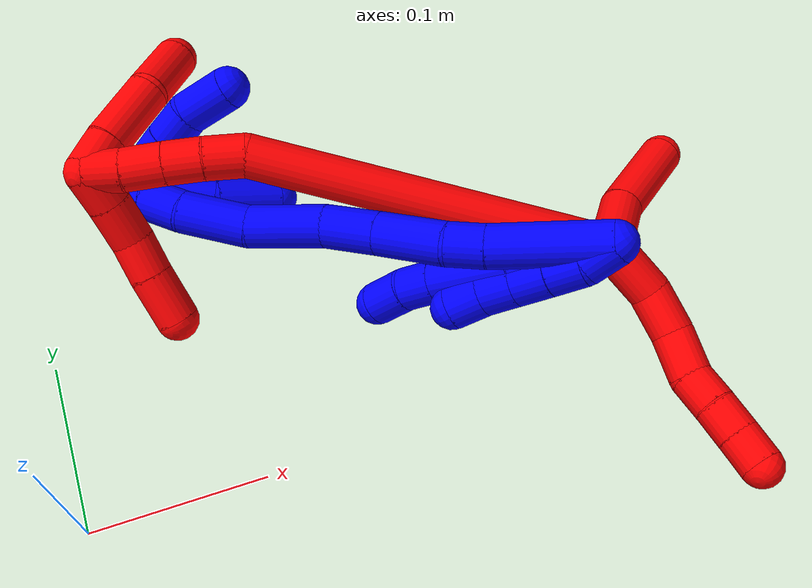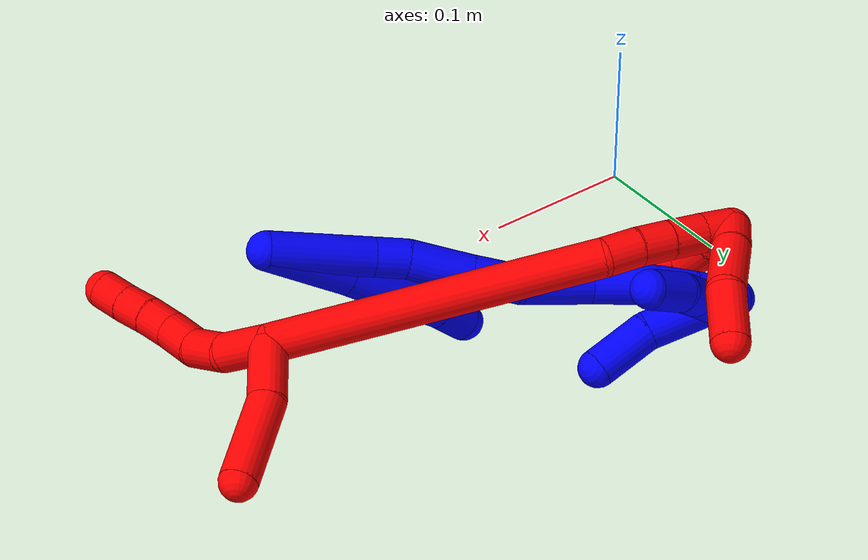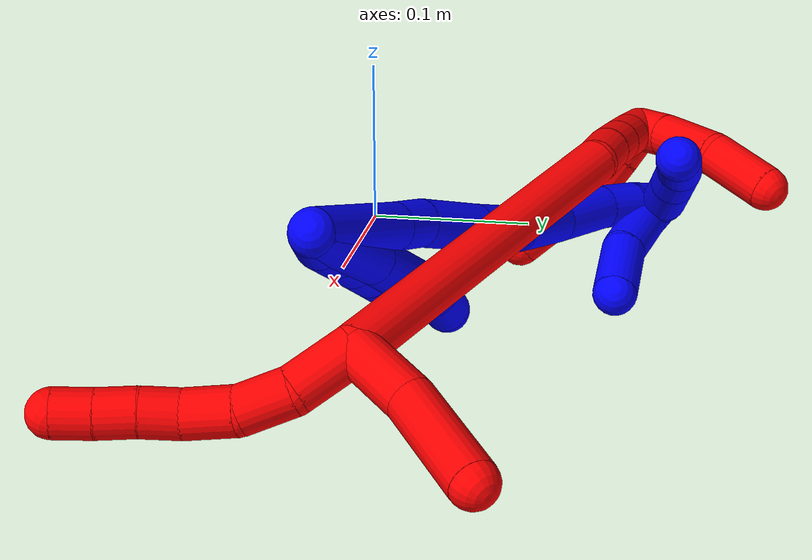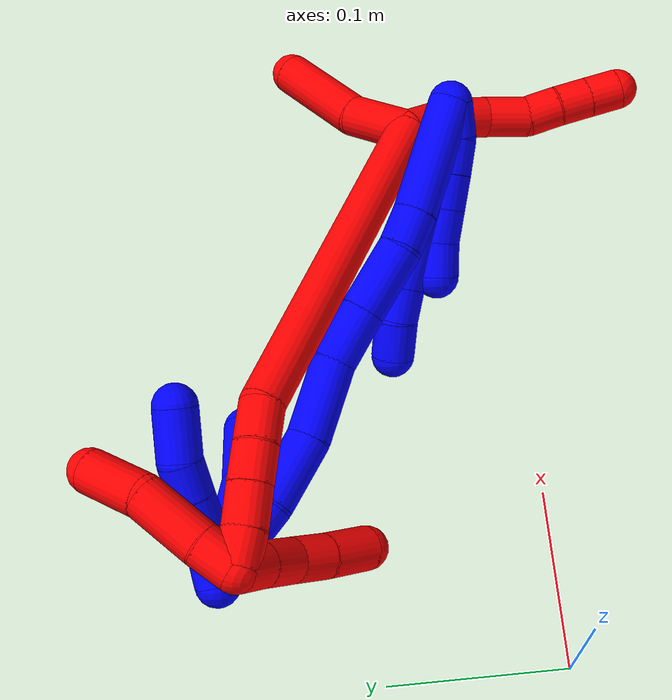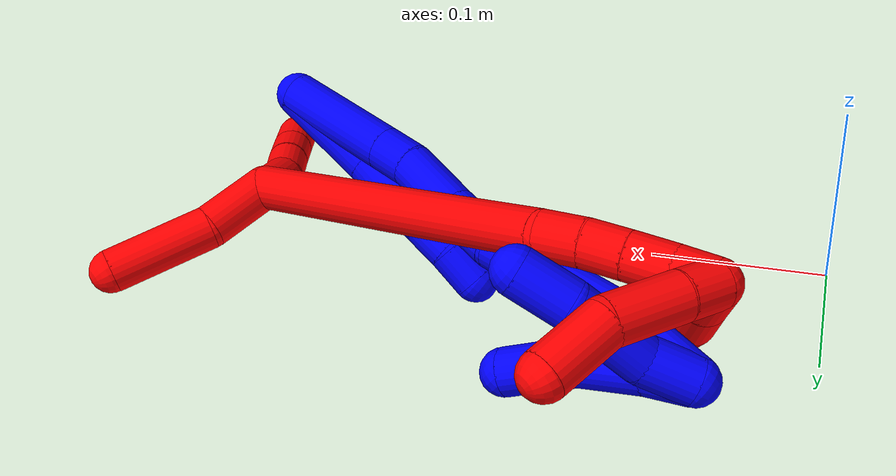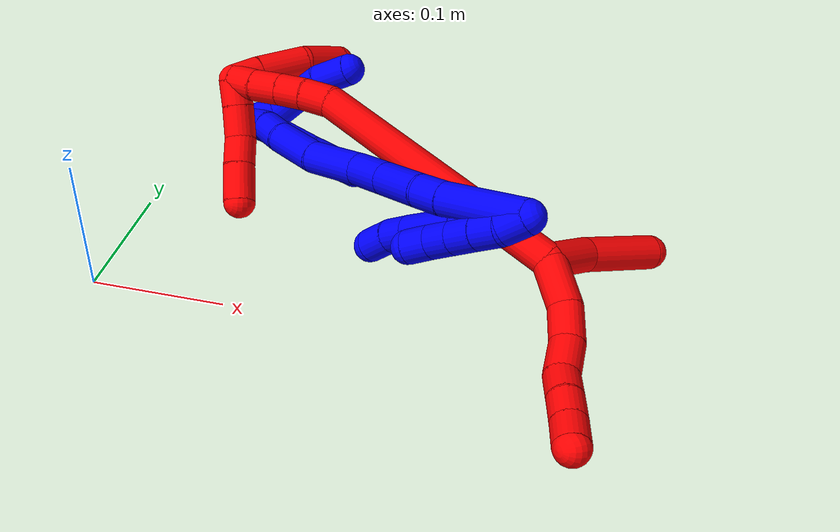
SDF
<sdf version="1.7">
 <world name="default">
  <plugin name="TubeGeneratorPlugin" filename="libtube_generator_plugin.so"/>
  <model name="photoneo_s_sensor">
   <static>1</static>
   <pose>0 0 2 1.57079 1.57079 3.14159</pose>
   <link name="link">
    <inertial><mass>0.1</mass></inertial>
    <sensor name="sensor" type="depth">
     <update_rate>30</update_rate>
     <camera>
      <horizontal_fov>1.22</horizontal_fov>
      <image><width>1920</width><height>1200</height><format>B8G8R8</format></image>
      <clip><near>0.1</near><far>4</far></clip>
      <depth_camera><output>points</output></depth_camera>
     </camera>
     <plugin name="camera_plugin" filename="libgazebo_ros_depth_camera.so">
      <baseline>0.2</baseline>
      <alwaysOn>1</alwaysOn>
      <updateRate>0.0</updateRate>
      <cameraName>camera_ir</cameraName>
      <imageTopicName>/camera/color/image_raw</imageTopicName>
      <cameraInfoTopicName>/camera/color/camera_info</cameraInfoTopicName>
      <depthImageTopicName>/camera/depth/image_raw</depthImageTopicName>
      <depthImageCameraInfoTopicName>/camera/depth/camera_info</depthImageCameraInfoTopicName>
      <pointCloudTopicName>/camera/depth/points</pointCloudTopicName>
      <frameName>fr_optical</frameName>
      <pointCloudCutoff>0.1</pointCloudCutoff>
      <pointCloudCutoffMax>2.0</pointCloudCutoffMax>
      <distortionK1>0</distortionK1>
      <distortionK2>0</distortionK2>
      <distortionK3>0</distortionK3>
      <distortionT1>0</distortionT1>
      <distortionT2>0</distortionT2>
      <CxPrime>0</CxPrime>
      <Cx>0</Cx>
      <Cy>0</Cy>
      <focalLength>0</focalLength>
      <hackBaseline>0</hackBaseline>
     </plugin>
    </sensor>
   </link>
  </model>
  <gravity>0 0 -9.8</gravity>
  <magnetic_field>6e-06 2.3e-05 -4.2e-05</magnetic_field>
  <atmosphere type="adiabatic"/>
  <physics name="default_physics" default="0" type="ode">
   <max_step_size>0.003</max_step_size>
   <real_time_factor>1</real_time_factor>
   <real_time_update_rate>1000</real_time_update_rate>
   <max_contacts>10000</max_contacts>
   <ode>
    <solver>
     <type>quick</type>
     <iters>100</iters>
     <sor>1.3</sor>
     <use_dynamic_moi_rescaling>0</use_dynamic_moi_rescaling>
    </solver>
    <constraints>
     <contact_max_correcting_vel>0</contact_max_correcting_vel>
     <contact_surface_layer>0.001</contact_surface_layer>
     <cfm>0</cfm>
     <erp>0.2</erp>
    </constraints>
   </ode>
  </physics>
  <scene><ambient>0.4 0.4 0.4 1</ambient><background>0.7 0.7 0.7 1</background><shadows>0</shadows></scene>
  <audio><device>default</device></audio>
  <spherical_coordinates>
   <surface_model>EARTH_WGS84</surface_model>
   <latitude_deg>0</latitude_deg>
   <longitude_deg>0</longitude_deg>
   <elevation>0</elevation>
   <heading_deg>0</heading_deg>
  </spherical_coordinates>
  <model name="bin">
   <static>1</static>
   <link name="bottom">
    <collision name="collision-bottom">
     <pose>0 0 -0.01 0 -0 0</pose>
     <geometry><box><size>0.8 0.6 0.02</size></box></geometry>
     <surface>
      <friction><ode><mu>100</mu><mu2>100</mu2></ode></friction>
      <contact><collide_bitmask>65535</collide_bitmask></contact>
     </surface>
    </collision>
   </link>
   <link name="west_wall">
    <collision name="collision-west_wall">
     <pose>-0.41 0 0.1 0 -0 0</pose>
     <geometry><box><size>0.02 0.6 0.2</size></box></geometry>
     <surface>
      <friction><ode><mu>100</mu><mu2>100</mu2></ode></friction>
      <contact><collide_bitmask>65535</collide_bitmask></contact>
     </surface>
    </collision>
   </link>
   <link name="east_wall">
    <collision name="collision-east_wall">
     <pose>0.41 0 0.1 0 -0 0</pose>
     <geometry><box><size>0.02 0.6 0.2</size></box></geometry>
     <surface>
      <friction><ode><mu>100</mu><mu2>100</mu2></ode></friction>
      <contact><collide_bitmask>65535</collide_bitmask></contact>
     </surface>
    </collision>
   </link>
   <link name="south_wall">
    <collision name="collision-south_wall">
     <pose>0 -0.31 0.1 0 -0 0</pose>
     <geometry><box><size>0.8 0.02 0.2</size></box></geometry>
     <surface>
      <friction><ode><mu>100</mu><mu2>100</mu2></ode></friction>
      <contact><collide_bitmask>65535</collide_bitmask></contact>
     </surface>
    </collision>
   </link>
   <link name="north_wall">
    <collision name="collision-north_wall">
     <pose>0 0.31 0.1 0 -0 0</pose>
     <geometry><box><size>0.8 0.02 0.2</size></box></geometry>
     <surface>
      <friction><ode><mu>100</mu><mu2>100</mu2></ode></friction>
      <contact><collide_bitmask>65535</collide_bitmask></contact>
     </surface>
    </collision>
   </link>
  </model>
  <model name="1">
   <static>0</static>
   <link name="1">
    <collision name="collision-cylinder-e_1_2_8">
     <pose>0.000139 0.009773 0.027738 -0.338739 0.004714 -0.000806</pose>
     <geometry><cylinder><radius>0.0125</radius><length>0.058819</length></cylinder></geometry>
     <surface>
      <friction><ode><mu>1.16</mu><mu2>1.16</mu2><slip1>0</slip1><slip2>0</slip2></ode></friction>
      <contact><ode><kp>1e+06</kp><kd>1</kd><max_vel>0</max_vel><min_depth>0.001</min_depth></ode></contact>
     </surface>
    </collision>
    <visual name="visual-cylinder-e_1_2_8">
     <pose>0.000139 0.009773 0.027738 -0.338739 0.004714 -0.000806</pose>
     <geometry><cylinder><radius>0.0125</radius><length>0.058819</length></cylinder></geometry>
     <material><ambient>0 0 1 1</ambient></material>
    </visual>
    <collision name="collision-cylinder-e_2_8_9">
     <pose>-0.000883 0.028095 0.078295 -0.358496 -0.047589 0.008624</pose>
     <geometry><cylinder><radius>0.0125</radius><length>0.048792</length></cylinder></geometry>
     <surface>
      <friction><ode><mu>1.16</mu><mu2>1.16</mu2><slip1>0</slip1><slip2>0</slip2></ode></friction>
      <contact><ode><kp>1e+06</kp><kd>1</kd><max_vel>0</max_vel><min_depth>0.001</min_depth></ode></contact>
     </surface>
    </collision>
    <visual name="visual-cylinder-e_2_8_9">
     <pose>-0.000883 0.028095 0.078295 -0.358496 -0.047589 0.008624</pose>
     <geometry><cylinder><radius>0.0125</radius><length>0.048792</length></cylinder></geometry>
     <material><ambient>0 0 1 1</ambient></material>
    </visual>
    <collision name="collision-cylinder-e_3_9_10">
     <pose>-0.002339 0.039596 0.110769 -0.296622 -0.02918 0.00436</pose>
     <geometry><cylinder><radius>0.0125</radius><length>0.0202</length></cylinder></geometry>
     <surface>
      <friction><ode><mu>1.16</mu><mu2>1.16</mu2><slip1>0</slip1><slip2>0</slip2></ode></friction>
      <contact><ode><kp>1e+06</kp><kd>1</kd><max_vel>0</max_vel><min_depth>0.001</min_depth></ode></contact>
     </surface>
    </collision>
    <visual name="visual-cylinder-e_3_9_10">
     <pose>-0.002339 0.039596 0.110769 -0.296622 -0.02918 0.00436</pose>
     <geometry><cylinder><radius>0.0125</radius><length>0.0202</length></cylinder></geometry>
     <material><ambient>0 0 1 1</ambient></material>
    </visual>
    <collision name="collision-cylinder-e_4_10_6">
     <pose>-0.004356 0.044228 0.131254 -0.153979 -0.155894 0.01205</pose>
     <geometry><cylinder><radius>0.0125</radius><length>0.022189</length></cylinder></geometry>
     <surface>
      <friction><ode><mu>1.16</mu><mu2>1.16</mu2><slip1>0</slip1><slip2>0</slip2></ode></friction>
      <contact><ode><kp>1e+06</kp><kd>1</kd><max_vel>0</max_vel><min_depth>0.001</min_depth></ode></contact>
     </surface>
    </collision>
    <visual name="visual-cylinder-e_4_10_6">
     <pose>-0.004356 0.044228 0.131254 -0.153979 -0.155894 0.01205</pose>
     <geometry><cylinder><radius>0.0125</radius><length>0.022189</length></cylinder></geometry>
     <material><ambient>0 0 1 1</ambient></material>
    </visual>
    <collision name="collision-cylinder-e_1_2_11">
     <pose>-2.7e-05 -0.000279 0.009996 0.027876 -0.002651 -3.7e-05</pose>
     <geometry><cylinder><radius>0.0125</radius><length>0.02</length></cylinder></geometry>
     <surface>
      <friction><ode><mu>1.16</mu><mu2>1.16</mu2><slip1>0</slip1><slip2>0</slip2></ode></friction>
      <contact><ode><kp>1e+06</kp><kd>1</kd><max_vel>0</max_vel><min_depth>0.001</min_depth></ode></contact>
     </surface>
    </collision>
    <visual name="visual-cylinder-e_1_2_11">
     <pose>-2.7e-05 -0.000279 0.009996 0.027876 -0.002651 -3.7e-05</pose>
     <geometry><cylinder><radius>0.0125</radius><length>0.02</length></cylinder></geometry>
     <material><ambient>0 0 1 1</ambient></material>
    </visual>
    <collision name="collision-cylinder-e_2_11_12">
     <pose>0.000122 0.001899 0.029684 -0.248211 0.017472 -0.00218</pose>
     <geometry><cylinder><radius>0.0125</radius><length>0.02</length></cylinder></geometry>
     <surface>
      <friction><ode><mu>1.16</mu><mu2>1.16</mu2><slip1>0</slip1><slip2>0</slip2></ode></friction>
      <contact><ode><kp>1e+06</kp><kd>1</kd><max_vel>0</max_vel><min_depth>0.001</min_depth></ode></contact>
     </surface>
    </collision>
    <visual name="visual-cylinder-e_2_11_12">
     <pose>0.000122 0.001899 0.029684 -0.248211 0.017472 -0.00218</pose>
     <geometry><cylinder><radius>0.0125</radius><length>0.02</length></cylinder></geometry>
     <material><ambient>0 0 1 1</ambient></material>
    </visual>
    <collision name="collision-cylinder-e_3_12_13">
     <pose>0.00021 0.006936 0.049037 -0.261026 -0.00861 0.00113</pose>
     <geometry><cylinder><radius>0.0125</radius><length>0.02</length></cylinder></geometry>
     <surface>
      <friction><ode><mu>1.16</mu><mu2>1.16</mu2><slip1>0</slip1><slip2>0</slip2></ode></friction>
      <contact><ode><kp>1e+06</kp><kd>1</kd><max_vel>0</max_vel><min_depth>0.001</min_depth></ode></contact>
     </surface>
    </collision>
    <visual name="visual-cylinder-e_3_12_13">
     <pose>0.00021 0.006936 0.049037 -0.261026 -0.00861 0.00113</pose>
     <geometry><cylinder><radius>0.0125</radius><length>0.02</length></cylinder></geometry>
     <material><ambient>0 0 1 1</ambient></material>
    </visual>
    <collision name="collision-cylinder-e_4_13_14">
     <pose>3.7e-05 0.012096 0.068359 -0.260864 -0.008765 0.00115</pose>
     <geometry><cylinder><radius>0.0125</radius><length>0.02</length></cylinder></geometry>
     <surface>
      <friction><ode><mu>1.16</mu><mu2>1.16</mu2><slip1>0</slip1><slip2>0</slip2></ode></friction>
      <contact><ode><kp>1e+06</kp><kd>1</kd><max_vel>0</max_vel><min_depth>0.001</min_depth></ode></contact>
     </surface>
    </collision>
    <visual name="visual-cylinder-e_4_13_14">
     <pose>3.7e-05 0.012096 0.068359 -0.260864 -0.008765 0.00115</pose>
     <geometry><cylinder><radius>0.0125</radius><length>0.02</length></cylinder></geometry>
     <material><ambient>0 0 1 1</ambient></material>
    </visual>
    <collision name="collision-cylinder-e_5_14_5">
     <pose>0.000746 0.015981 0.087903 -0.131413 0.079835 -0.005256</pose>
     <geometry><cylinder><radius>0.0125</radius><length>0.02</length></cylinder></geometry>
     <surface>
      <friction><ode><mu>1.16</mu><mu2>1.16</mu2><slip1>0</slip1><slip2>0</slip2></ode></friction>
      <contact><ode><kp>1e+06</kp><kd>1</kd><max_vel>0</max_vel><min_depth>0.001</min_depth></ode></contact>
     </surface>
    </collision>
    <visual name="visual-cylinder-e_5_14_5">
     <pose>0.000746 0.015981 0.087903 -0.131413 0.079835 -0.005256</pose>
     <geometry><cylinder><radius>0.0125</radius><length>0.02</length></cylinder></geometry>
     <material><ambient>0 0 1 1</ambient></material>
    </visual>
    <collision name="collision-cylinder-e_1_2_15">
     <pose>0.008605 0.015533 0.028914 -0.49297 0.256404 -0.064845</pose>
     <geometry><cylinder><radius>0.0125</radius><length>0.067863</length></cylinder></geometry>
     <surface>
      <friction><ode><mu>1.16</mu><mu2>1.16</mu2><slip1>0</slip1><slip2>0</slip2></ode></friction>
      <contact><ode><kp>1e+06</kp><kd>1</kd><max_vel>0</max_vel><min_depth>0.001</min_depth></ode></contact>
     </surface>
    </collision>
    <visual name="visual-cylinder-e_1_2_15">
     <pose>0.008605 0.015533 0.028914 -0.49297 0.256404 -0.064845</pose>
     <geometry><cylinder><radius>0.0125</radius><length>0.067863</length></cylinder></geometry>
     <material><ambient>0 0 1 1</ambient></material>
    </visual>
    <collision name="collision-cylinder-e_2_15_16">
     <pose>0.020164 0.036889 0.066597 -0.586204 0.273577 -0.083035</pose>
     <geometry><cylinder><radius>0.0125</radius><length>0.021864</length></cylinder></geometry>
     <surface>
      <friction><ode><mu>1.16</mu><mu2>1.16</mu2><slip1>0</slip1><slip2>0</slip2></ode></friction>
      <contact><ode><kp>1e+06</kp><kd>1</kd><max_vel>0</max_vel><min_depth>0.001</min_depth></ode></contact>
     </surface>
    </collision>
    <visual name="visual-cylinder-e_2_15_16">
     <pose>0.020164 0.036889 0.066597 -0.586204 0.273577 -0.083035</pose>
     <geometry><cylinder><radius>0.0125</radius><length>0.021864</length></cylinder></geometry>
     <material><ambient>0 0 1 1</ambient></material>
    </visual>
    <collision name="collision-cylinder-e_3_16_17">
     <pose>0.025181 0.055378 0.090925 -0.683273 0.102499 -0.036474</pose>
     <geometry><cylinder><radius>0.0125</radius><length>0.040339</length></cylinder></geometry>
     <surface>
      <friction><ode><mu>1.16</mu><mu2>1.16</mu2><slip1>0</slip1><slip2>0</slip2></ode></friction>
      <contact><ode><kp>1e+06</kp><kd>1</kd><max_vel>0</max_vel><min_depth>0.001</min_depth></ode></contact>
     </surface>
    </collision>
    <visual name="visual-cylinder-e_3_16_17">
     <pose>0.025181 0.055378 0.090925 -0.683273 0.102499 -0.036474</pose>
     <geometry><cylinder><radius>0.0125</radius><length>0.040339</length></cylinder></geometry>
     <material><ambient>0 0 1 1</ambient></material>
    </visual>
    <collision name="collision-cylinder-e_4_17_18">
     <pose>0.02948 0.078134 0.119305 -0.666698 0.136141 -0.047206</pose>
     <geometry><cylinder><radius>0.0125</radius><length>0.032933</length></cylinder></geometry>
     <surface>
      <friction><ode><mu>1.16</mu><mu2>1.16</mu2><slip1>0</slip1><slip2>0</slip2></ode></friction>
      <contact><ode><kp>1e+06</kp><kd>1</kd><max_vel>0</max_vel><min_depth>0.001</min_depth></ode></contact>
     </surface>
    </collision>
    <visual name="visual-cylinder-e_4_17_18">
     <pose>0.02948 0.078134 0.119305 -0.666698 0.136141 -0.047206</pose>
     <geometry><cylinder><radius>0.0125</radius><length>0.032933</length></cylinder></geometry>
     <material><ambient>0 0 1 1</ambient></material>
    </visual>
    <collision name="collision-cylinder-e_5_18_19">
     <pose>0.038838 0.098754 0.150781 -0.51393 0.321009 -0.085034</pose>
     <geometry><cylinder><radius>0.0125</radius><length>0.045151</length></cylinder></geometry>
     <surface>
      <friction><ode><mu>1.16</mu><mu2>1.16</mu2><slip1>0</slip1><slip2>0</slip2></ode></friction>
      <contact><ode><kp>1e+06</kp><kd>1</kd><max_vel>0</max_vel><min_depth>0.001</min_depth></ode></contact>
     </surface>
    </collision>
    <visual name="visual-cylinder-e_5_18_19">
     <pose>0.038838 0.098754 0.150781 -0.51393 0.321009 -0.085034</pose>
     <geometry><cylinder><radius>0.0125</radius><length>0.045151</length></cylinder></geometry>
     <material><ambient>0 0 1 1</ambient></material>
    </visual>
    <collision name="collision-cylinder-e_6_19_20">
     <pose>0.052878 0.122255 0.183643 -0.739882 0.345177 -0.134998</pose>
     <geometry><cylinder><radius>0.0125</radius><length>0.040885</length></cylinder></geometry>
     <surface>
      <friction><ode><mu>1.16</mu><mu2>1.16</mu2><slip1>0</slip1><slip2>0</slip2></ode></friction>
      <contact><ode><kp>1e+06</kp><kd>1</kd><max_vel>0</max_vel><min_depth>0.001</min_depth></ode></contact>
     </surface>
    </collision>
    <visual name="visual-cylinder-e_6_19_20">
     <pose>0.052878 0.122255 0.183643 -0.739882 0.345177 -0.134998</pose>
     <geometry><cylinder><radius>0.0125</radius><length>0.040885</length></cylinder></geometry>
     <material><ambient>0 0 1 1</ambient></material>
    </visual>
    <collision name="collision-cylinder-e_7_20_21">
     <pose>0.062286 0.144129 0.205665 -0.850531 0.207235 -0.094125</pose>
     <geometry><cylinder><radius>0.0125</radius><length>0.024213</length></cylinder></geometry>
     <surface>
      <friction><ode><mu>1.16</mu><mu2>1.16</mu2><slip1>0</slip1><slip2>0</slip2></ode></friction>
      <contact><ode><kp>1e+06</kp><kd>1</kd><max_vel>0</max_vel><min_depth>0.001</min_depth></ode></contact>
     </surface>
    </collision>
    <visual name="visual-cylinder-e_7_20_21">
     <pose>0.062286 0.144129 0.205665 -0.850531 0.207235 -0.094125</pose>
     <geometry><cylinder><radius>0.0125</radius><length>0.024213</length></cylinder></geometry>
     <material><ambient>0 0 1 1</ambient></material>
    </visual>
    <collision name="collision-cylinder-e_8_21_1">
     <pose>0.066904 0.161195 0.223861 -0.666198 0.159707 -0.055361</pose>
     <geometry><cylinder><radius>0.0125</radius><length>0.026751</length></cylinder></geometry>
     <surface>
      <friction><ode><mu>1.16</mu><mu2>1.16</mu2><slip1>0</slip1><slip2>0</slip2></ode></friction>
      <contact><ode><kp>1e+06</kp><kd>1</kd><max_vel>0</max_vel><min_depth>0.001</min_depth></ode></contact>
     </surface>
    </collision>
    <visual name="visual-cylinder-e_8_21_1">
     <pose>0.066904 0.161195 0.223861 -0.666198 0.159707 -0.055361</pose>
     <geometry><cylinder><radius>0.0125</radius><length>0.026751</length></cylinder></geometry>
     <material><ambient>0 0 1 1</ambient></material>
    </visual>
    <collision name="collision-cylinder-e_1_1_22">
     <pose>0.062285 0.164642 0.225688 2.63796 -0.604428 -1.76172</pose>
     <geometry><cylinder><radius>0.0125</radius><length>0.023741</length></cylinder></geometry>
     <surface>
      <friction><ode><mu>1.16</mu><mu2>1.16</mu2><slip1>0</slip1><slip2>0</slip2></ode></friction>
      <contact><ode><kp>1e+06</kp><kd>1</kd><max_vel>0</max_vel><min_depth>0.001</min_depth></ode></contact>
     </surface>
    </collision>
    <visual name="visual-cylinder-e_1_1_22">
     <pose>0.062285 0.164642 0.225688 2.63796 -0.604428 -1.76172</pose>
     <geometry><cylinder><radius>0.0125</radius><length>0.023741</length></cylinder></geometry>
     <material><ambient>0 0 1 1</ambient></material>
    </visual>
    <collision name="collision-cylinder-e_2_22_23">
     <pose>0.043378 0.15243 0.204972 2.58908 -0.705186 -1.82866</pose>
     <geometry><cylinder><radius>0.0125</radius><length>0.037524</length></cylinder></geometry>
     <surface>
      <friction><ode><mu>1.16</mu><mu2>1.16</mu2><slip1>0</slip1><slip2>0</slip2></ode></friction>
      <contact><ode><kp>1e+06</kp><kd>1</kd><max_vel>0</max_vel><min_depth>0.001</min_depth></ode></contact>
     </surface>
    </collision>
    <visual name="visual-cylinder-e_2_22_23">
     <pose>0.043378 0.15243 0.204972 2.58908 -0.705186 -1.82866</pose>
     <geometry><cylinder><radius>0.0125</radius><length>0.037524</length></cylinder></geometry>
     <material><ambient>0 0 1 1</ambient></material>
    </visual>
    <collision name="collision-cylinder-e_3_23_4">
     <pose>0.015776 0.141005 0.181799 2.79904 -0.922758 -2.47197</pose>
     <geometry><cylinder><radius>0.0125</radius><length>0.038735</length></cylinder></geometry>
     <surface>
      <friction><ode><mu>1.16</mu><mu2>1.16</mu2><slip1>0</slip1><slip2>0</slip2></ode></friction>
      <contact><ode><kp>1e+06</kp><kd>1</kd><max_vel>0</max_vel><min_depth>0.001</min_depth></ode></contact>
     </surface>
    </collision>
    <visual name="visual-cylinder-e_3_23_4">
     <pose>0.015776 0.141005 0.181799 2.79904 -0.922758 -2.47197</pose>
     <geometry><cylinder><radius>0.0125</radius><length>0.038735</length></cylinder></geometry>
     <material><ambient>0 0 1 1</ambient></material>
    </visual>
    <collision name="collision-cylinder-e_1_1_24">
     <pose>0.065809 0.170625 0.22133 -3.04362 -0.243429 2.3792</pose>
     <geometry><cylinder><radius>0.0125</radius><length>0.026737</length></cylinder></geometry>
     <surface>
      <friction><ode><mu>1.16</mu><mu2>1.16</mu2><slip1>0</slip1><slip2>0</slip2></ode></friction>
      <contact><ode><kp>1e+06</kp><kd>1</kd><max_vel>0</max_vel><min_depth>0.001</min_depth></ode></contact>
     </surface>
    </collision>
    <visual name="visual-cylinder-e_1_1_24">
     <pose>0.065809 0.170625 0.22133 -3.04362 -0.243429 2.3792</pose>
     <geometry><cylinder><radius>0.0125</radius><length>0.026737</length></cylinder></geometry>
     <material><ambient>0 0 1 1</ambient></material>
    </visual>
    <collision name="collision-cylinder-e_2_24_25">
     <pose>0.063525 0.174425 0.19671 -2.92866 0.078131 -0.701238</pose>
     <geometry><cylinder><radius>0.0125</radius><length>0.024031</length></cylinder></geometry>
     <surface>
      <friction><ode><mu>1.16</mu><mu2>1.16</mu2><slip1>0</slip1><slip2>0</slip2></ode></friction>
      <contact><ode><kp>1e+06</kp><kd>1</kd><max_vel>0</max_vel><min_depth>0.001</min_depth></ode></contact>
     </surface>
    </collision>
    <visual name="visual-cylinder-e_2_24_25">
     <pose>0.063525 0.174425 0.19671 -2.92866 0.078131 -0.701238</pose>
     <geometry><cylinder><radius>0.0125</radius><length>0.024031</length></cylinder></geometry>
     <material><ambient>0 0 1 1</ambient></material>
    </visual>
    <collision name="collision-cylinder-e_3_25_26">
     <pose>0.065012 0.178907 0.174926 -2.9504 0.053482 -0.544055</pose>
     <geometry><cylinder><radius>0.0125</radius><length>0.020555</length></cylinder></geometry>
     <surface>
      <friction><ode><mu>1.16</mu><mu2>1.16</mu2><slip1>0</slip1><slip2>0</slip2></ode></friction>
      <contact><ode><kp>1e+06</kp><kd>1</kd><max_vel>0</max_vel><min_depth>0.001</min_depth></ode></contact>
     </surface>
    </collision>
    <visual name="visual-cylinder-e_3_25_26">
     <pose>0.065012 0.178907 0.174926 -2.9504 0.053482 -0.544055</pose>
     <geometry><cylinder><radius>0.0125</radius><length>0.020555</length></cylinder></geometry>
     <material><ambient>0 0 1 1</ambient></material>
    </visual>
    <collision name="collision-cylinder-e_4_26_3">
     <pose>0.063809 0.180198 0.150634 3.09529 -0.1225 -2.4195</pose>
     <geometry><cylinder><radius>0.0125</radius><length>0.028677</length></cylinder></geometry>
     <surface>
      <friction><ode><mu>1.16</mu><mu2>1.16</mu2><slip1>0</slip1><slip2>0</slip2></ode></friction>
      <contact><ode><kp>1e+06</kp><kd>1</kd><max_vel>0</max_vel><min_depth>0.001</min_depth></ode></contact>
     </surface>
    </collision>
    <visual name="visual-cylinder-e_4_26_3">
     <pose>0.063809 0.180198 0.150634 3.09529 -0.1225 -2.4195</pose>
     <geometry><cylinder><radius>0.0125</radius><length>0.028677</length></cylinder></geometry>
     <material><ambient>0 0 1 1</ambient></material>
    </visual>
    <collision name="collision-sphere-3">
     <pose>0.062057 0.17954 0.136418 0 -0 0</pose>
     <geometry><sphere><radius>0.0125</radius></sphere></geometry>
     <surface>
      <friction><ode><mu>1.16</mu><mu2>1.16</mu2><slip1>0</slip1><slip2>0</slip2></ode></friction>
      <contact><ode><kp>1e+06</kp><kd>1</kd><max_vel>0</max_vel><min_depth>0.001</min_depth></ode></contact>
     </surface>
    </collision>
    <visual name="visual-sphere-3">
     <pose>0.062057 0.17954 0.136418 0 -0 0</pose>
     <geometry><sphere><radius>0.0125</radius></sphere></geometry>
     <material><ambient>0 0 1 1</ambient></material>
    </visual>
    <collision name="collision-sphere-26">
     <pose>0.065561 0.180857 0.16485 0 -0 0</pose>
     <geometry><sphere><radius>0.0125</radius></sphere></geometry>
     <surface>
      <friction><ode><mu>1.16</mu><mu2>1.16</mu2><slip1>0</slip1><slip2>0</slip2></ode></friction>
      <contact><ode><kp>1e+06</kp><kd>1</kd><max_vel>0</max_vel><min_depth>0.001</min_depth></ode></contact>
     </surface>
    </collision>
    <visual name="visual-sphere-26">
     <pose>0.065561 0.180857 0.16485 0 -0 0</pose>
     <geometry><sphere><radius>0.0125</radius></sphere></geometry>
     <material><ambient>0 0 1 1</ambient></material>
    </visual>
    <collision name="collision-sphere-25">
     <pose>0.064462 0.176957 0.185002 0 -0 0</pose>
     <geometry><sphere><radius>0.0125</radius></sphere></geometry>
     <surface>
      <friction><ode><mu>1.16</mu><mu2>1.16</mu2><slip1>0</slip1><slip2>0</slip2></ode></friction>
      <contact><ode><kp>1e+06</kp><kd>1</kd><max_vel>0</max_vel><min_depth>0.001</min_depth></ode></contact>
     </surface>
    </collision>
    <visual name="visual-sphere-25">
     <pose>0.064462 0.176957 0.185002 0 -0 0</pose>
     <geometry><sphere><radius>0.0125</radius></sphere></geometry>
     <material><ambient>0 0 1 1</ambient></material>
    </visual>
    <collision name="collision-sphere-24">
     <pose>0.062587 0.171894 0.208418 0 -0 0</pose>
     <geometry><sphere><radius>0.0125</radius></sphere></geometry>
     <surface>
      <friction><ode><mu>1.16</mu><mu2>1.16</mu2><slip1>0</slip1><slip2>0</slip2></ode></friction>
      <contact><ode><kp>1e+06</kp><kd>1</kd><max_vel>0</max_vel><min_depth>0.001</min_depth></ode></contact>
     </surface>
    </collision>
    <visual name="visual-sphere-24">
     <pose>0.062587 0.171894 0.208418 0 -0 0</pose>
     <geometry><sphere><radius>0.0125</radius></sphere></geometry>
     <material><ambient>0 0 1 1</ambient></material>
    </visual>
    <collision name="collision-sphere-4">
     <pose>0.000335 0.137078 0.170788 0 -0 0</pose>
     <geometry><sphere><radius>0.0125</radius></sphere></geometry>
     <surface>
      <friction><ode><mu>1.16</mu><mu2>1.16</mu2><slip1>0</slip1><slip2>0</slip2></ode></friction>
      <contact><ode><kp>1e+06</kp><kd>1</kd><max_vel>0</max_vel><min_depth>0.001</min_depth></ode></contact>
     </surface>
    </collision>
    <visual name="visual-sphere-4">
     <pose>0.000335 0.137078 0.170788 0 -0 0</pose>
     <geometry><sphere><radius>0.0125</radius></sphere></geometry>
     <material><ambient>0 0 1 1</ambient></material>
    </visual>
    <collision name="collision-sphere-23">
     <pose>0.031217 0.144931 0.192811 0 -0 0</pose>
     <geometry><sphere><radius>0.0125</radius></sphere></geometry>
     <surface>
      <friction><ode><mu>1.16</mu><mu2>1.16</mu2><slip1>0</slip1><slip2>0</slip2></ode></friction>
      <contact><ode><kp>1e+06</kp><kd>1</kd><max_vel>0</max_vel><min_depth>0.001</min_depth></ode></contact>
     </surface>
    </collision>
    <visual name="visual-sphere-23">
     <pose>0.031217 0.144931 0.192811 0 -0 0</pose>
     <geometry><sphere><radius>0.0125</radius></sphere></geometry>
     <material><ambient>0 0 1 1</ambient></material>
    </visual>
    <collision name="collision-sphere-22">
     <pose>0.055539 0.159928 0.217133 0 -0 0</pose>
     <geometry><sphere><radius>0.0125</radius></sphere></geometry>
     <surface>
      <friction><ode><mu>1.16</mu><mu2>1.16</mu2><slip1>0</slip1><slip2>0</slip2></ode></friction>
      <contact><ode><kp>1e+06</kp><kd>1</kd><max_vel>0</max_vel><min_depth>0.001</min_depth></ode></contact>
     </surface>
    </collision>
    <visual name="visual-sphere-22">
     <pose>0.055539 0.159928 0.217133 0 -0 0</pose>
     <geometry><sphere><radius>0.0125</radius></sphere></geometry>
     <material><ambient>0 0 1 1</ambient></material>
    </visual>
    <collision name="collision-sphere-1">
     <pose>0.069031 0.169356 0.234243 0 -0 0</pose>
     <geometry><sphere><radius>0.0125</radius></sphere></geometry>
     <surface>
      <friction><ode><mu>1.16</mu><mu2>1.16</mu2><slip1>0</slip1><slip2>0</slip2></ode></friction>
      <contact><ode><kp>1e+06</kp><kd>1</kd><max_vel>0</max_vel><min_depth>0.001</min_depth></ode></contact>
     </surface>
    </collision>
    <visual name="visual-sphere-1">
     <pose>0.069031 0.169356 0.234243 0 -0 0</pose>
     <geometry><sphere><radius>0.0125</radius></sphere></geometry>
     <material><ambient>0 0 1 1</ambient></material>
    </visual>
    <collision name="collision-sphere-21">
     <pose>0.064777 0.153034 0.213479 0 -0 0</pose>
     <geometry><sphere><radius>0.0125</radius></sphere></geometry>
     <surface>
      <friction><ode><mu>1.16</mu><mu2>1.16</mu2><slip1>0</slip1><slip2>0</slip2></ode></friction>
      <contact><ode><kp>1e+06</kp><kd>1</kd><max_vel>0</max_vel><min_depth>0.001</min_depth></ode></contact>
     </surface>
    </collision>
    <visual name="visual-sphere-21">
     <pose>0.064777 0.153034 0.213479 0 -0 0</pose>
     <geometry><sphere><radius>0.0125</radius></sphere></geometry>
     <material><ambient>0 0 1 1</ambient></material>
    </visual>
    <collision name="collision-sphere-11">
     <pose>-5.3e-05 -0.000557 0.019992 0 -0 0</pose>
     <geometry><sphere><radius>0.0125</radius></sphere></geometry>
     <surface>
      <friction><ode><mu>1.16</mu><mu2>1.16</mu2><slip1>0</slip1><slip2>0</slip2></ode></friction>
      <contact><ode><kp>1e+06</kp><kd>1</kd><max_vel>0</max_vel><min_depth>0.001</min_depth></ode></contact>
     </surface>
    </collision>
    <visual name="visual-sphere-11">
     <pose>-5.3e-05 -0.000557 0.019992 0 -0 0</pose>
     <geometry><sphere><radius>0.0125</radius></sphere></geometry>
     <material><ambient>0 0 1 1</ambient></material>
    </visual>
    <collision name="collision-sphere-6">
     <pose>-0.006078 0.045909 0.142085 0 -0 0</pose>
     <geometry><sphere><radius>0.0125</radius></sphere></geometry>
     <surface>
      <friction><ode><mu>1.16</mu><mu2>1.16</mu2><slip1>0</slip1><slip2>0</slip2></ode></friction>
      <contact><ode><kp>1e+06</kp><kd>1</kd><max_vel>0</max_vel><min_depth>0.001</min_depth></ode></contact>
     </surface>
    </collision>
    <visual name="visual-sphere-6">
     <pose>-0.006078 0.045909 0.142085 0 -0 0</pose>
     <geometry><sphere><radius>0.0125</radius></sphere></geometry>
     <material><ambient>0 0 1 1</ambient></material>
    </visual>
    <collision name="collision-sphere-10">
     <pose>-0.002633 0.042547 0.120424 0 -0 0</pose>
     <geometry><sphere><radius>0.0125</radius></sphere></geometry>
     <surface>
      <friction><ode><mu>1.16</mu><mu2>1.16</mu2><slip1>0</slip1><slip2>0</slip2></ode></friction>
      <contact><ode><kp>1e+06</kp><kd>1</kd><max_vel>0</max_vel><min_depth>0.001</min_depth></ode></contact>
     </surface>
    </collision>
    <visual name="visual-sphere-10">
     <pose>-0.002633 0.042547 0.120424 0 -0 0</pose>
     <geometry><sphere><radius>0.0125</radius></sphere></geometry>
     <material><ambient>0 0 1 1</ambient></material>
    </visual>
    <collision name="collision-sphere-9">
     <pose>-0.002044 0.036645 0.101114 0 -0 0</pose>
     <geometry><sphere><radius>0.0125</radius></sphere></geometry>
     <surface>
      <friction><ode><mu>1.16</mu><mu2>1.16</mu2><slip1>0</slip1><slip2>0</slip2></ode></friction>
      <contact><ode><kp>1e+06</kp><kd>1</kd><max_vel>0</max_vel><min_depth>0.001</min_depth></ode></contact>
     </surface>
    </collision>
    <visual name="visual-sphere-9">
     <pose>-0.002044 0.036645 0.101114 0 -0 0</pose>
     <geometry><sphere><radius>0.0125</radius></sphere></geometry>
     <material><ambient>0 0 1 1</ambient></material>
    </visual>
    <collision name="collision-sphere-2">
     <geometry><sphere><radius>0.0125</radius></sphere></geometry>
     <surface>
      <friction><ode><mu>1.16</mu><mu2>1.16</mu2><slip1>0</slip1><slip2>0</slip2></ode></friction>
      <contact><ode><kp>1e+06</kp><kd>1</kd><max_vel>0</max_vel><min_depth>0.001</min_depth></ode></contact>
     </surface>
    </collision>
    <visual name="visual-sphere-2">
     <geometry><sphere><radius>0.0125</radius></sphere></geometry>
     <material><ambient>0 0 1 1</ambient></material>
    </visual>
    <collision name="collision-sphere-19">
     <pose>0.045961 0.109285 0.169436 0 -0 0</pose>
     <geometry><sphere><radius>0.0125</radius></sphere></geometry>
     <surface>
      <friction><ode><mu>1.16</mu><mu2>1.16</mu2><slip1>0</slip1><slip2>0</slip2></ode></friction>
      <contact><ode><kp>1e+06</kp><kd>1</kd><max_vel>0</max_vel><min_depth>0.001</min_depth></ode></contact>
     </surface>
    </collision>
    <visual name="visual-sphere-19">
     <pose>0.045961 0.109285 0.169436 0 -0 0</pose>
     <geometry><sphere><radius>0.0125</radius></sphere></geometry>
     <material><ambient>0 0 1 1</ambient></material>
    </visual>
    <collision name="collision-sphere-8">
     <pose>0.000277 0.019545 0.055476 0 -0 0</pose>
     <geometry><sphere><radius>0.0125</radius></sphere></geometry>
     <surface>
      <friction><ode><mu>1.16</mu><mu2>1.16</mu2><slip1>0</slip1><slip2>0</slip2></ode></friction>
      <contact><ode><kp>1e+06</kp><kd>1</kd><max_vel>0</max_vel><min_depth>0.001</min_depth></ode></contact>
     </surface>
    </collision>
    <visual name="visual-sphere-8">
     <pose>0.000277 0.019545 0.055476 0 -0 0</pose>
     <geometry><sphere><radius>0.0125</radius></sphere></geometry>
     <material><ambient>0 0 1 1</ambient></material>
    </visual>
    <collision name="collision-sphere-12">
     <pose>0.000296 0.004355 0.039376 0 -0 0</pose>
     <geometry><sphere><radius>0.0125</radius></sphere></geometry>
     <surface>
      <friction><ode><mu>1.16</mu><mu2>1.16</mu2><slip1>0</slip1><slip2>0</slip2></ode></friction>
      <contact><ode><kp>1e+06</kp><kd>1</kd><max_vel>0</max_vel><min_depth>0.001</min_depth></ode></contact>
     </surface>
    </collision>
    <visual name="visual-sphere-12">
     <pose>0.000296 0.004355 0.039376 0 -0 0</pose>
     <geometry><sphere><radius>0.0125</radius></sphere></geometry>
     <material><ambient>0 0 1 1</ambient></material>
    </visual>
    <collision name="collision-sphere-13">
     <pose>0.000124 0.009516 0.058698 0 -0 0</pose>
     <geometry><sphere><radius>0.0125</radius></sphere></geometry>
     <surface>
      <friction><ode><mu>1.16</mu><mu2>1.16</mu2><slip1>0</slip1><slip2>0</slip2></ode></friction>
      <contact><ode><kp>1e+06</kp><kd>1</kd><max_vel>0</max_vel><min_depth>0.001</min_depth></ode></contact>
     </surface>
    </collision>
    <visual name="visual-sphere-13">
     <pose>0.000124 0.009516 0.058698 0 -0 0</pose>
     <geometry><sphere><radius>0.0125</radius></sphere></geometry>
     <material><ambient>0 0 1 1</ambient></material>
    </visual>
    <collision name="collision-sphere-14">
     <pose>-5.1e-05 0.014675 0.078021 0 -0 0</pose>
     <geometry><sphere><radius>0.0125</radius></sphere></geometry>
     <surface>
      <friction><ode><mu>1.16</mu><mu2>1.16</mu2><slip1>0</slip1><slip2>0</slip2></ode></friction>
      <contact><ode><kp>1e+06</kp><kd>1</kd><max_vel>0</max_vel><min_depth>0.001</min_depth></ode></contact>
     </surface>
    </collision>
    <visual name="visual-sphere-14">
     <pose>-5.1e-05 0.014675 0.078021 0 -0 0</pose>
     <geometry><sphere><radius>0.0125</radius></sphere></geometry>
     <material><ambient>0 0 1 1</ambient></material>
    </visual>
    <collision name="collision-sphere-5">
     <pose>0.001544 0.017287 0.097785 0 -0 0</pose>
     <geometry><sphere><radius>0.0125</radius></sphere></geometry>
     <surface>
      <friction><ode><mu>1.16</mu><mu2>1.16</mu2><slip1>0</slip1><slip2>0</slip2></ode></friction>
      <contact><ode><kp>1e+06</kp><kd>1</kd><max_vel>0</max_vel><min_depth>0.001</min_depth></ode></contact>
     </surface>
    </collision>
    <visual name="visual-sphere-5">
     <pose>0.001544 0.017287 0.097785 0 -0 0</pose>
     <geometry><sphere><radius>0.0125</radius></sphere></geometry>
     <material><ambient>0 0 1 1</ambient></material>
    </visual>
    <collision name="collision-sphere-15">
     <pose>0.01721 0.031066 0.057828 0 -0 0</pose>
     <geometry><sphere><radius>0.0125</radius></sphere></geometry>
     <surface>
      <friction><ode><mu>1.16</mu><mu2>1.16</mu2><slip1>0</slip1><slip2>0</slip2></ode></friction>
      <contact><ode><kp>1e+06</kp><kd>1</kd><max_vel>0</max_vel><min_depth>0.001</min_depth></ode></contact>
     </surface>
    </collision>
    <visual name="visual-sphere-15">
     <pose>0.01721 0.031066 0.057828 0 -0 0</pose>
     <geometry><sphere><radius>0.0125</radius></sphere></geometry>
     <material><ambient>0 0 1 1</ambient></material>
    </visual>
    <collision name="collision-sphere-16">
     <pose>0.023118 0.042711 0.075365 0 -0 0</pose>
     <geometry><sphere><radius>0.0125</radius></sphere></geometry>
     <surface>
      <friction><ode><mu>1.16</mu><mu2>1.16</mu2><slip1>0</slip1><slip2>0</slip2></ode></friction>
      <contact><ode><kp>1e+06</kp><kd>1</kd><max_vel>0</max_vel><min_depth>0.001</min_depth></ode></contact>
     </surface>
    </collision>
    <visual name="visual-sphere-16">
     <pose>0.023118 0.042711 0.075365 0 -0 0</pose>
     <geometry><sphere><radius>0.0125</radius></sphere></geometry>
     <material><ambient>0 0 1 1</ambient></material>
    </visual>
    <collision name="collision-sphere-17">
     <pose>0.027245 0.068045 0.106484 0 -0 0</pose>
     <geometry><sphere><radius>0.0125</radius></sphere></geometry>
     <surface>
      <friction><ode><mu>1.16</mu><mu2>1.16</mu2><slip1>0</slip1><slip2>0</slip2></ode></friction>
      <contact><ode><kp>1e+06</kp><kd>1</kd><max_vel>0</max_vel><min_depth>0.001</min_depth></ode></contact>
     </surface>
    </collision>
    <visual name="visual-sphere-17">
     <pose>0.027245 0.068045 0.106484 0 -0 0</pose>
     <geometry><sphere><radius>0.0125</radius></sphere></geometry>
     <material><ambient>0 0 1 1</ambient></material>
    </visual>
    <collision name="collision-sphere-18">
     <pose>0.031715 0.088222 0.132125 0 -0 0</pose>
     <geometry><sphere><radius>0.0125</radius></sphere></geometry>
     <surface>
      <friction><ode><mu>1.16</mu><mu2>1.16</mu2><slip1>0</slip1><slip2>0</slip2></ode></friction>
      <contact><ode><kp>1e+06</kp><kd>1</kd><max_vel>0</max_vel><min_depth>0.001</min_depth></ode></contact>
     </surface>
    </collision>
    <visual name="visual-sphere-18">
     <pose>0.031715 0.088222 0.132125 0 -0 0</pose>
     <geometry><sphere><radius>0.0125</radius></sphere></geometry>
     <material><ambient>0 0 1 1</ambient></material>
    </visual>
    <collision name="collision-sphere-20">
     <pose>0.059795 0.135224 0.19785 0 -0 0</pose>
     <geometry><sphere><radius>0.0125</radius></sphere></geometry>
     <surface>
      <friction><ode><mu>1.16</mu><mu2>1.16</mu2><slip1>0</slip1><slip2>0</slip2></ode></friction>
      <contact><ode><kp>1e+06</kp><kd>1</kd><max_vel>0</max_vel><min_depth>0.001</min_depth></ode></contact>
     </surface>
    </collision>
    <visual name="visual-sphere-20">
     <pose>0.059795 0.135224 0.19785 0 -0 0</pose>
     <geometry><sphere><radius>0.0125</radius></sphere></geometry>
     <material><ambient>0 0 1 1</ambient></material>
    </visual>
    <inertial>
     <pose>0.026984 0.081434 0.120603 0 -0 0</pose>
     <mass>0.75</mass>
     <inertia>
      <ixx>8.1e-05</ixx>
      <ixy>0</ixy>
      <ixz>0</ixz>
      <iyy>0.000105</iyy>
      <iyz>0</iyz>
      <izz>-2.2e-05</izz>
     </inertia>
    </inertial>
   </link>
   <pose>0.305384 0.032568 0.092451 2.91006 -0.932992 -2.84096</pose>
  </model>
  <model name="2">
   <static>0</static>
   <link name="2">
    <collision name="collision-cylinder-e_1_2_8">
     <pose>0.012534 -0.011779 0.00163 1.43331 0.811687 0.716379</pose>
     <geometry><cylinder><radius>0.0125</radius><length>0.034554</length></cylinder></geometry>
     <surface>
      <friction><ode><mu>1.16</mu><mu2>1.16</mu2><slip1>0</slip1><slip2>0</slip2></ode></friction>
      <contact><ode><kp>1e+06</kp><kd>1</kd><max_vel>0</max_vel><min_depth>0.001</min_depth></ode></contact>
     </surface>
    </collision>
    <visual name="visual-cylinder-e_1_2_8">
     <pose>0.012534 -0.011779 0.00163 1.43331 0.811687 0.716379</pose>
     <geometry><cylinder><radius>0.0125</radius><length>0.034554</length></cylinder></geometry>
     <material><ambient>1 0 0 1</ambient></material>
    </visual>
    <collision name="collision-cylinder-e_2_8_9">
     <pose>0.033791 -0.032285 0.008898 0.997152 0.698469 0.391462</pose>
     <geometry><cylinder><radius>0.0125</radius><length>0.027134</length></cylinder></geometry>
     <surface>
      <friction><ode><mu>1.16</mu><mu2>1.16</mu2><slip1>0</slip1><slip2>0</slip2></ode></friction>
      <contact><ode><kp>1e+06</kp><kd>1</kd><max_vel>0</max_vel><min_depth>0.001</min_depth></ode></contact>
     </surface>
    </collision>
    <visual name="visual-cylinder-e_2_8_9">
     <pose>0.033791 -0.032285 0.008898 0.997152 0.698469 0.391462</pose>
     <geometry><cylinder><radius>0.0125</radius><length>0.027134</length></cylinder></geometry>
     <material><ambient>1 0 0 1</ambient></material>
    </visual>
    <collision name="collision-cylinder-e_3_9_10">
     <pose>0.050401 -0.047575 0.023609 0.626285 0.613563 0.20443</pose>
     <geometry><cylinder><radius>0.0125</radius><length>0.027391</length></cylinder></geometry>
     <surface>
      <friction><ode><mu>1.16</mu><mu2>1.16</mu2><slip1>0</slip1><slip2>0</slip2></ode></friction>
      <contact><ode><kp>1e+06</kp><kd>1</kd><max_vel>0</max_vel><min_depth>0.001</min_depth></ode></contact>
     </surface>
    </collision>
    <visual name="visual-cylinder-e_3_9_10">
     <pose>0.050401 -0.047575 0.023609 0.626285 0.613563 0.20443</pose>
     <geometry><cylinder><radius>0.0125</radius><length>0.027391</length></cylinder></geometry>
     <material><ambient>1 0 0 1</ambient></material>
    </visual>
    <collision name="collision-cylinder-e_4_10_11">
     <pose>0.066362 -0.056788 0.038571 0.422782 0.896198 0.205592</pose>
     <geometry><cylinder><radius>0.0125</radius><length>0.02068</length></cylinder></geometry>
     <surface>
      <friction><ode><mu>1.16</mu><mu2>1.16</mu2><slip1>0</slip1><slip2>0</slip2></ode></friction>
      <contact><ode><kp>1e+06</kp><kd>1</kd><max_vel>0</max_vel><min_depth>0.001</min_depth></ode></contact>
     </surface>
    </collision>
    <visual name="visual-cylinder-e_4_10_11">
     <pose>0.066362 -0.056788 0.038571 0.422782 0.896198 0.205592</pose>
     <geometry><cylinder><radius>0.0125</radius><length>0.02068</length></cylinder></geometry>
     <material><ambient>1 0 0 1</ambient></material>
    </visual>
    <collision name="collision-cylinder-e_5_11_12">
     <pose>0.082218 -0.062861 0.049928 0.559318 0.878601 0.268291</pose>
     <geometry><cylinder><radius>0.0125</radius><length>0.020213</length></cylinder></geometry>
     <surface>
      <friction><ode><mu>1.16</mu><mu2>1.16</mu2><slip1>0</slip1><slip2>0</slip2></ode></friction>
      <contact><ode><kp>1e+06</kp><kd>1</kd><max_vel>0</max_vel><min_depth>0.001</min_depth></ode></contact>
     </surface>
    </collision>
    <visual name="visual-cylinder-e_5_11_12">
     <pose>0.082218 -0.062861 0.049928 0.559318 0.878601 0.268291</pose>
     <geometry><cylinder><radius>0.0125</radius><length>0.020213</length></cylinder></geometry>
     <material><ambient>1 0 0 1</ambient></material>
    </visual>
    <collision name="collision-cylinder-e_6_12_6">
     <pose>0.097579 -0.069283 0.061209 0.476372 0.858829 0.221448</pose>
     <geometry><cylinder><radius>0.0125</radius><length>0.020028</length></cylinder></geometry>
     <surface>
      <friction><ode><mu>1.16</mu><mu2>1.16</mu2><slip1>0</slip1><slip2>0</slip2></ode></friction>
      <contact><ode><kp>1e+06</kp><kd>1</kd><max_vel>0</max_vel><min_depth>0.001</min_depth></ode></contact>
     </surface>
    </collision>
    <visual name="visual-cylinder-e_6_12_6">
     <pose>0.097579 -0.069283 0.061209 0.476372 0.858829 0.221448</pose>
     <geometry><cylinder><radius>0.0125</radius><length>0.020028</length></cylinder></geometry>
     <material><ambient>1 0 0 1</ambient></material>
    </visual>
    <collision name="collision-cylinder-e_1_2_13">
     <pose>-0.001929 -0.000521 -0.020053 3.11562 -0.095883 -2.61296</pose>
     <geometry><cylinder><radius>0.0125</radius><length>0.040305</length></cylinder></geometry>
     <surface>
      <friction><ode><mu>1.16</mu><mu2>1.16</mu2><slip1>0</slip1><slip2>0</slip2></ode></friction>
      <contact><ode><kp>1e+06</kp><kd>1</kd><max_vel>0</max_vel><min_depth>0.001</min_depth></ode></contact>
     </surface>
    </collision>
    <visual name="visual-cylinder-e_1_2_13">
     <pose>-0.001929 -0.000521 -0.020053 3.11562 -0.095883 -2.61296</pose>
     <geometry><cylinder><radius>0.0125</radius><length>0.040305</length></cylinder></geometry>
     <material><ambient>1 0 0 1</ambient></material>
    </visual>
    <collision name="collision-cylinder-e_2_13_5">
     <pose>0.001231 -0.001074 -0.069517 3.14048 0.171371 3.12869</pose>
     <geometry><cylinder><radius>0.0125</radius><length>0.059695</length></cylinder></geometry>
     <surface>
      <friction><ode><mu>1.16</mu><mu2>1.16</mu2><slip1>0</slip1><slip2>0</slip2></ode></friction>
      <contact><ode><kp>1e+06</kp><kd>1</kd><max_vel>0</max_vel><min_depth>0.001</min_depth></ode></contact>
     </surface>
    </collision>
    <visual name="visual-cylinder-e_2_13_5">
     <pose>0.001231 -0.001074 -0.069517 3.14048 0.171371 3.12869</pose>
     <geometry><cylinder><radius>0.0125</radius><length>0.059695</length></cylinder></geometry>
     <material><ambient>1 0 0 1</ambient></material>
    </visual>
    <collision name="collision-cylinder-e_1_2_14">
     <pose>-0.096337 0.031328 0.030274 -0.802513 -1.1461 0.534454</pose>
     <geometry><cylinder><radius>0.0125</radius><length>0.211459</length></cylinder></geometry>
     <surface>
      <friction><ode><mu>1.16</mu><mu2>1.16</mu2><slip1>0</slip1><slip2>0</slip2></ode></friction>
      <contact><ode><kp>1e+06</kp><kd>1</kd><max_vel>0</max_vel><min_depth>0.001</min_depth></ode></contact>
     </surface>
    </collision>
    <visual name="visual-cylinder-e_1_2_14">
     <pose>-0.096337 0.031328 0.030274 -0.802513 -1.1461 0.534454</pose>
     <geometry><cylinder><radius>0.0125</radius><length>0.211459</length></cylinder></geometry>
     <material><ambient>1 0 0 1</ambient></material>
    </visual>
    <collision name="collision-cylinder-e_2_14_15">
     <pose>-0.202817 0.063141 0.06616 -0.086027 -1.06384 0.050647</pose>
     <geometry><cylinder><radius>0.0125</radius><length>0.023204</length></cylinder></geometry>
     <surface>
      <friction><ode><mu>1.16</mu><mu2>1.16</mu2><slip1>0</slip1><slip2>0</slip2></ode></friction>
      <contact><ode><kp>1e+06</kp><kd>1</kd><max_vel>0</max_vel><min_depth>0.001</min_depth></ode></contact>
     </surface>
    </collision>
    <visual name="visual-cylinder-e_2_14_15">
     <pose>-0.202817 0.063141 0.06616 -0.086027 -1.06384 0.050647</pose>
     <geometry><cylinder><radius>0.0125</radius><length>0.023204</length></cylinder></geometry>
     <material><ambient>1 0 0 1</ambient></material>
    </visual>
    <collision name="collision-cylinder-e_3_15_16">
     <pose>-0.222504 0.063195 0.076608 0.088692 -1.10023 -0.054414</pose>
     <geometry><cylinder><radius>0.0125</radius><length>0.021417</length></cylinder></geometry>
     <surface>
      <friction><ode><mu>1.16</mu><mu2>1.16</mu2><slip1>0</slip1><slip2>0</slip2></ode></friction>
      <contact><ode><kp>1e+06</kp><kd>1</kd><max_vel>0</max_vel><min_depth>0.001</min_depth></ode></contact>
     </surface>
    </collision>
    <visual name="visual-cylinder-e_3_15_16">
     <pose>-0.222504 0.063195 0.076608 0.088692 -1.10023 -0.054414</pose>
     <geometry><cylinder><radius>0.0125</radius><length>0.021417</length></cylinder></geometry>
     <material><ambient>1 0 0 1</ambient></material>
    </visual>
    <collision name="collision-cylinder-e_4_16_17">
     <pose>-0.242408 0.061902 0.08681 0.159303 -1.08764 -0.096449</pose>
     <geometry><cylinder><radius>0.0125</radius><length>0.023397</length></cylinder></geometry>
     <surface>
      <friction><ode><mu>1.16</mu><mu2>1.16</mu2><slip1>0</slip1><slip2>0</slip2></ode></friction>
      <contact><ode><kp>1e+06</kp><kd>1</kd><max_vel>0</max_vel><min_depth>0.001</min_depth></ode></contact>
     </surface>
    </collision>
    <visual name="visual-cylinder-e_4_16_17">
     <pose>-0.242408 0.061902 0.08681 0.159303 -1.08764 -0.096449</pose>
     <geometry><cylinder><radius>0.0125</radius><length>0.023397</length></cylinder></geometry>
     <material><ambient>1 0 0 1</ambient></material>
    </visual>
    <collision name="collision-cylinder-e_5_17_1">
     <pose>-0.262201 0.060941 0.096213 0.024701 -1.16632 -0.016296</pose>
     <geometry><cylinder><radius>0.0125</radius><length>0.020523</length></cylinder></geometry>
     <surface>
      <friction><ode><mu>1.16</mu><mu2>1.16</mu2><slip1>0</slip1><slip2>0</slip2></ode></friction>
      <contact><ode><kp>1e+06</kp><kd>1</kd><max_vel>0</max_vel><min_depth>0.001</min_depth></ode></contact>
     </surface>
    </collision>
    <visual name="visual-cylinder-e_5_17_1">
     <pose>-0.262201 0.060941 0.096213 0.024701 -1.16632 -0.016296</pose>
     <geometry><cylinder><radius>0.0125</radius><length>0.020523</length></cylinder></geometry>
     <material><ambient>1 0 0 1</ambient></material>
    </visual>
    <collision name="collision-cylinder-e_1_1_18">
     <pose>-0.271027 0.064359 0.08999 -2.81124 0.055862 -0.332114</pose>
     <geometry><cylinder><radius>0.0125</radius><length>0.021726</length></cylinder></geometry>
     <surface>
      <friction><ode><mu>1.16</mu><mu2>1.16</mu2><slip1>0</slip1><slip2>0</slip2></ode></friction>
      <contact><ode><kp>1e+06</kp><kd>1</kd><max_vel>0</max_vel><min_depth>0.001</min_depth></ode></contact>
     </surface>
    </collision>
    <visual name="visual-cylinder-e_1_1_18">
     <pose>-0.271027 0.064359 0.08999 -2.81124 0.055862 -0.332114</pose>
     <geometry><cylinder><radius>0.0125</radius><length>0.021726</length></cylinder></geometry>
     <material><ambient>1 0 0 1</ambient></material>
    </visual>
    <collision name="collision-cylinder-e_2_18_19">
     <pose>-0.268133 0.072918 0.060159 -2.88955 0.112742 -0.838053</pose>
     <geometry><cylinder><radius>0.0125</radius><length>0.040679</length></cylinder></geometry>
     <surface>
      <friction><ode><mu>1.16</mu><mu2>1.16</mu2><slip1>0</slip1><slip2>0</slip2></ode></friction>
      <contact><ode><kp>1e+06</kp><kd>1</kd><max_vel>0</max_vel><min_depth>0.001</min_depth></ode></contact>
     </surface>
    </collision>
    <visual name="visual-cylinder-e_2_18_19">
     <pose>-0.268133 0.072918 0.060159 -2.88955 0.112742 -0.838053</pose>
     <geometry><cylinder><radius>0.0125</radius><length>0.040679</length></cylinder></geometry>
     <material><ambient>1 0 0 1</ambient></material>
    </visual>
    <collision name="collision-cylinder-e_3_19_4">
     <pose>-0.267843 0.077934 0.021896 3.14031 -0.106537 -3.11752</pose>
     <geometry><cylinder><radius>0.0125</radius><length>0.037595</length></cylinder></geometry>
     <surface>
      <friction><ode><mu>1.16</mu><mu2>1.16</mu2><slip1>0</slip1><slip2>0</slip2></ode></friction>
      <contact><ode><kp>1e+06</kp><kd>1</kd><max_vel>0</max_vel><min_depth>0.001</min_depth></ode></contact>
     </surface>
    </collision>
    <visual name="visual-cylinder-e_3_19_4">
     <pose>-0.267843 0.077934 0.021896 3.14031 -0.106537 -3.11752</pose>
     <geometry><cylinder><radius>0.0125</radius><length>0.037595</length></cylinder></geometry>
     <material><ambient>1 0 0 1</ambient></material>
    </visual>
    <collision name="collision-cylinder-e_1_1_20">
     <pose>-0.267338 0.051052 0.099942 1.60227 0.413409 0.426238</pose>
     <geometry><cylinder><radius>0.0125</radius><length>0.021389</length></cylinder></geometry>
     <surface>
      <friction><ode><mu>1.16</mu><mu2>1.16</mu2><slip1>0</slip1><slip2>0</slip2></ode></friction>
      <contact><ode><kp>1e+06</kp><kd>1</kd><max_vel>0</max_vel><min_depth>0.001</min_depth></ode></contact>
     </surface>
    </collision>
    <visual name="visual-cylinder-e_1_1_20">
     <pose>-0.267338 0.051052 0.099942 1.60227 0.413409 0.426238</pose>
     <geometry><cylinder><radius>0.0125</radius><length>0.021389</length></cylinder></geometry>
     <material><ambient>1 0 0 1</ambient></material>
    </visual>
    <collision name="collision-cylinder-e_2_20_21">
     <pose>-0.257956 0.029384 0.099921 1.5466 0.404346 0.394931</pose>
     <geometry><cylinder><radius>0.0125</radius><length>0.025852</length></cylinder></geometry>
     <surface>
      <friction><ode><mu>1.16</mu><mu2>1.16</mu2><slip1>0</slip1><slip2>0</slip2></ode></friction>
      <contact><ode><kp>1e+06</kp><kd>1</kd><max_vel>0</max_vel><min_depth>0.001</min_depth></ode></contact>
     </surface>
    </collision>
    <visual name="visual-cylinder-e_2_20_21">
     <pose>-0.257956 0.029384 0.099921 1.5466 0.404346 0.394931</pose>
     <geometry><cylinder><radius>0.0125</radius><length>0.025852</length></cylinder></geometry>
     <material><ambient>1 0 0 1</ambient></material>
    </visual>
    <collision name="collision-cylinder-e_3_21_22">
     <pose>-0.247012 0.008193 0.103088 1.27087 0.541303 0.403666</pose>
     <geometry><cylinder><radius>0.0125</radius><length>0.022743</length></cylinder></geometry>
     <surface>
      <friction><ode><mu>1.16</mu><mu2>1.16</mu2><slip1>0</slip1><slip2>0</slip2></ode></friction>
      <contact><ode><kp>1e+06</kp><kd>1</kd><max_vel>0</max_vel><min_depth>0.001</min_depth></ode></contact>
     </surface>
    </collision>
    <visual name="visual-cylinder-e_3_21_22">
     <pose>-0.247012 0.008193 0.103088 1.27087 0.541303 0.403666</pose>
     <geometry><cylinder><radius>0.0125</radius><length>0.022743</length></cylinder></geometry>
     <material><ambient>1 0 0 1</ambient></material>
    </visual>
    <collision name="collision-cylinder-e_4_22_3">
     <pose>-0.233034 -0.013385 0.108943 1.33285 0.57154 0.454165</pose>
     <geometry><cylinder><radius>0.0125</radius><length>0.030017</length></cylinder></geometry>
     <surface>
      <friction><ode><mu>1.16</mu><mu2>1.16</mu2><slip1>0</slip1><slip2>0</slip2></ode></friction>
      <contact><ode><kp>1e+06</kp><kd>1</kd><max_vel>0</max_vel><min_depth>0.001</min_depth></ode></contact>
     </surface>
    </collision>
    <visual name="visual-cylinder-e_4_22_3">
     <pose>-0.233034 -0.013385 0.108943 1.33285 0.57154 0.454165</pose>
     <geometry><cylinder><radius>0.0125</radius><length>0.030017</length></cylinder></geometry>
     <material><ambient>1 0 0 1</ambient></material>
    </visual>
    <collision name="collision-sphere-3">
     <pose>-0.224916 -0.025653 0.111918 0 -0 0</pose>
     <geometry><sphere><radius>0.0125</radius></sphere></geometry>
     <surface>
      <friction><ode><mu>1.16</mu><mu2>1.16</mu2><slip1>0</slip1><slip2>0</slip2></ode></friction>
      <contact><ode><kp>1e+06</kp><kd>1</kd><max_vel>0</max_vel><min_depth>0.001</min_depth></ode></contact>
     </surface>
    </collision>
    <visual name="visual-sphere-3">
     <pose>-0.224916 -0.025653 0.111918 0 -0 0</pose>
     <geometry><sphere><radius>0.0125</radius></sphere></geometry>
     <material><ambient>1 0 0 1</ambient></material>
    </visual>
    <collision name="collision-sphere-22">
     <pose>-0.241153 -0.001118 0.105968 0 -0 0</pose>
     <geometry><sphere><radius>0.0125</radius></sphere></geometry>
     <surface>
      <friction><ode><mu>1.16</mu><mu2>1.16</mu2><slip1>0</slip1><slip2>0</slip2></ode></friction>
      <contact><ode><kp>1e+06</kp><kd>1</kd><max_vel>0</max_vel><min_depth>0.001</min_depth></ode></contact>
     </surface>
    </collision>
    <visual name="visual-sphere-22">
     <pose>-0.241153 -0.001118 0.105968 0 -0 0</pose>
     <geometry><sphere><radius>0.0125</radius></sphere></geometry>
     <material><ambient>1 0 0 1</ambient></material>
    </visual>
    <collision name="collision-sphere-21">
     <pose>-0.252871 0.017504 0.100209 0 -0 0</pose>
     <geometry><sphere><radius>0.0125</radius></sphere></geometry>
     <surface>
      <friction><ode><mu>1.16</mu><mu2>1.16</mu2><slip1>0</slip1><slip2>0</slip2></ode></friction>
      <contact><ode><kp>1e+06</kp><kd>1</kd><max_vel>0</max_vel><min_depth>0.001</min_depth></ode></contact>
     </surface>
    </collision>
    <visual name="visual-sphere-21">
     <pose>-0.252871 0.017504 0.100209 0 -0 0</pose>
     <geometry><sphere><radius>0.0125</radius></sphere></geometry>
     <material><ambient>1 0 0 1</ambient></material>
    </visual>
    <collision name="collision-sphere-20">
     <pose>-0.263041 0.041264 0.099634 0 -0 0</pose>
     <geometry><sphere><radius>0.0125</radius></sphere></geometry>
     <surface>
      <friction><ode><mu>1.16</mu><mu2>1.16</mu2><slip1>0</slip1><slip2>0</slip2></ode></friction>
      <contact><ode><kp>1e+06</kp><kd>1</kd><max_vel>0</max_vel><min_depth>0.001</min_depth></ode></contact>
     </surface>
    </collision>
    <visual name="visual-sphere-20">
     <pose>-0.263041 0.041264 0.099634 0 -0 0</pose>
     <geometry><sphere><radius>0.0125</radius></sphere></geometry>
     <material><ambient>1 0 0 1</ambient></material>
    </visual>
    <collision name="collision-sphere-4">
     <pose>-0.269842 0.07791 0.003206 0 -0 0</pose>
     <geometry><sphere><radius>0.0125</radius></sphere></geometry>
     <surface>
      <friction><ode><mu>1.16</mu><mu2>1.16</mu2><slip1>0</slip1><slip2>0</slip2></ode></friction>
      <contact><ode><kp>1e+06</kp><kd>1</kd><max_vel>0</max_vel><min_depth>0.001</min_depth></ode></contact>
     </surface>
    </collision>
    <visual name="visual-sphere-4">
     <pose>-0.269842 0.07791 0.003206 0 -0 0</pose>
     <geometry><sphere><radius>0.0125</radius></sphere></geometry>
     <material><ambient>1 0 0 1</ambient></material>
    </visual>
    <collision name="collision-sphere-12">
     <pose>0.089998 -0.066283 0.055395 0 -0 0</pose>
     <geometry><sphere><radius>0.0125</radius></sphere></geometry>
     <surface>
      <friction><ode><mu>1.16</mu><mu2>1.16</mu2><slip1>0</slip1><slip2>0</slip2></ode></friction>
      <contact><ode><kp>1e+06</kp><kd>1</kd><max_vel>0</max_vel><min_depth>0.001</min_depth></ode></contact>
     </surface>
    </collision>
    <visual name="visual-sphere-12">
     <pose>0.089998 -0.066283 0.055395 0 -0 0</pose>
     <geometry><sphere><radius>0.0125</radius></sphere></geometry>
     <material><ambient>1 0 0 1</ambient></material>
    </visual>
    <collision name="collision-sphere-11">
     <pose>0.074437 -0.059438 0.044461 0 -0 0</pose>
     <geometry><sphere><radius>0.0125</radius></sphere></geometry>
     <surface>
      <friction><ode><mu>1.16</mu><mu2>1.16</mu2><slip1>0</slip1><slip2>0</slip2></ode></friction>
      <contact><ode><kp>1e+06</kp><kd>1</kd><max_vel>0</max_vel><min_depth>0.001</min_depth></ode></contact>
     </surface>
    </collision>
    <visual name="visual-sphere-11">
     <pose>0.074437 -0.059438 0.044461 0 -0 0</pose>
     <geometry><sphere><radius>0.0125</radius></sphere></geometry>
     <material><ambient>1 0 0 1</ambient></material>
    </visual>
    <collision name="collision-sphere-10">
     <pose>0.058287 -0.054138 0.032681 0 -0 0</pose>
     <geometry><sphere><radius>0.0125</radius></sphere></geometry>
     <surface>
      <friction><ode><mu>1.16</mu><mu2>1.16</mu2><slip1>0</slip1><slip2>0</slip2></ode></friction>
      <contact><ode><kp>1e+06</kp><kd>1</kd><max_vel>0</max_vel><min_depth>0.001</min_depth></ode></contact>
     </surface>
    </collision>
    <visual name="visual-sphere-10">
     <pose>0.058287 -0.054138 0.032681 0 -0 0</pose>
     <geometry><sphere><radius>0.0125</radius></sphere></geometry>
     <material><ambient>1 0 0 1</ambient></material>
    </visual>
    <collision name="collision-sphere-9">
     <pose>0.042516 -0.041012 0.014537 0 -0 0</pose>
     <geometry><sphere><radius>0.0125</radius></sphere></geometry>
     <surface>
      <friction><ode><mu>1.16</mu><mu2>1.16</mu2><slip1>0</slip1><slip2>0</slip2></ode></friction>
      <contact><ode><kp>1e+06</kp><kd>1</kd><max_vel>0</max_vel><min_depth>0.001</min_depth></ode></contact>
     </surface>
    </collision>
    <visual name="visual-sphere-9">
     <pose>0.042516 -0.041012 0.014537 0 -0 0</pose>
     <geometry><sphere><radius>0.0125</radius></sphere></geometry>
     <material><ambient>1 0 0 1</ambient></material>
    </visual>
    <collision name="collision-sphere-2">
     <geometry><sphere><radius>0.0125</radius></sphere></geometry>
     <surface>
      <friction><ode><mu>1.16</mu><mu2>1.16</mu2><slip1>0</slip1><slip2>0</slip2></ode></friction>
      <contact><ode><kp>1e+06</kp><kd>1</kd><max_vel>0</max_vel><min_depth>0.001</min_depth></ode></contact>
     </surface>
    </collision>
    <visual name="visual-sphere-2">
     <geometry><sphere><radius>0.0125</radius></sphere></geometry>
     <material><ambient>1 0 0 1</ambient></material>
    </visual>
    <collision name="collision-sphere-19">
     <pose>-0.265844 0.077958 0.040587 0 -0 0</pose>
     <geometry><sphere><radius>0.0125</radius></sphere></geometry>
     <surface>
      <friction><ode><mu>1.16</mu><mu2>1.16</mu2><slip1>0</slip1><slip2>0</slip2></ode></friction>
      <contact><ode><kp>1e+06</kp><kd>1</kd><max_vel>0</max_vel><min_depth>0.001</min_depth></ode></contact>
     </surface>
    </collision>
    <visual name="visual-sphere-19">
     <pose>-0.265844 0.077958 0.040587 0 -0 0</pose>
     <geometry><sphere><radius>0.0125</radius></sphere></geometry>
     <material><ambient>1 0 0 1</ambient></material>
    </visual>
    <collision name="collision-sphere-8">
     <pose>0.025067 -0.023558 0.00326 0 -0 0</pose>
     <geometry><sphere><radius>0.0125</radius></sphere></geometry>
     <surface>
      <friction><ode><mu>1.16</mu><mu2>1.16</mu2><slip1>0</slip1><slip2>0</slip2></ode></friction>
      <contact><ode><kp>1e+06</kp><kd>1</kd><max_vel>0</max_vel><min_depth>0.001</min_depth></ode></contact>
     </surface>
    </collision>
    <visual name="visual-sphere-8">
     <pose>0.025067 -0.023558 0.00326 0 -0 0</pose>
     <geometry><sphere><radius>0.0125</radius></sphere></geometry>
     <material><ambient>1 0 0 1</ambient></material>
    </visual>
    <collision name="collision-sphere-6">
     <pose>0.105161 -0.072283 0.067023 0 -0 0</pose>
     <geometry><sphere><radius>0.0125</radius></sphere></geometry>
     <surface>
      <friction><ode><mu>1.16</mu><mu2>1.16</mu2><slip1>0</slip1><slip2>0</slip2></ode></friction>
      <contact><ode><kp>1e+06</kp><kd>1</kd><max_vel>0</max_vel><min_depth>0.001</min_depth></ode></contact>
     </surface>
    </collision>
    <visual name="visual-sphere-6">
     <pose>0.105161 -0.072283 0.067023 0 -0 0</pose>
     <geometry><sphere><radius>0.0125</radius></sphere></geometry>
     <material><ambient>1 0 0 1</ambient></material>
    </visual>
    <collision name="collision-sphere-13">
     <pose>-0.003859 -0.001042 -0.040106 0 -0 0</pose>
     <geometry><sphere><radius>0.0125</radius></sphere></geometry>
     <surface>
      <friction><ode><mu>1.16</mu><mu2>1.16</mu2><slip1>0</slip1><slip2>0</slip2></ode></friction>
      <contact><ode><kp>1e+06</kp><kd>1</kd><max_vel>0</max_vel><min_depth>0.001</min_depth></ode></contact>
     </surface>
    </collision>
    <visual name="visual-sphere-13">
     <pose>-0.003859 -0.001042 -0.040106 0 -0 0</pose>
     <geometry><sphere><radius>0.0125</radius></sphere></geometry>
     <material><ambient>1 0 0 1</ambient></material>
    </visual>
    <collision name="collision-sphere-5">
     <pose>0.006321 -0.001107 -0.098927 0 -0 0</pose>
     <geometry><sphere><radius>0.0125</radius></sphere></geometry>
     <surface>
      <friction><ode><mu>1.16</mu><mu2>1.16</mu2><slip1>0</slip1><slip2>0</slip2></ode></friction>
      <contact><ode><kp>1e+06</kp><kd>1</kd><max_vel>0</max_vel><min_depth>0.001</min_depth></ode></contact>
     </surface>
    </collision>
    <visual name="visual-sphere-5">
     <pose>0.006321 -0.001107 -0.098927 0 -0 0</pose>
     <geometry><sphere><radius>0.0125</radius></sphere></geometry>
     <material><ambient>1 0 0 1</ambient></material>
    </visual>
    <collision name="collision-sphere-14">
     <pose>-0.192674 0.062657 0.060548 0 -0 0</pose>
     <geometry><sphere><radius>0.0125</radius></sphere></geometry>
     <surface>
      <friction><ode><mu>1.16</mu><mu2>1.16</mu2><slip1>0</slip1><slip2>0</slip2></ode></friction>
      <contact><ode><kp>1e+06</kp><kd>1</kd><max_vel>0</max_vel><min_depth>0.001</min_depth></ode></contact>
     </surface>
    </collision>
    <visual name="visual-sphere-14">
     <pose>-0.192674 0.062657 0.060548 0 -0 0</pose>
     <geometry><sphere><radius>0.0125</radius></sphere></geometry>
     <material><ambient>1 0 0 1</ambient></material>
    </visual>
    <collision name="collision-sphere-15">
     <pose>-0.212959 0.063625 0.071772 0 -0 0</pose>
     <geometry><sphere><radius>0.0125</radius></sphere></geometry>
     <surface>
      <friction><ode><mu>1.16</mu><mu2>1.16</mu2><slip1>0</slip1><slip2>0</slip2></ode></friction>
      <contact><ode><kp>1e+06</kp><kd>1</kd><max_vel>0</max_vel><min_depth>0.001</min_depth></ode></contact>
     </surface>
    </collision>
    <visual name="visual-sphere-15">
     <pose>-0.212959 0.063625 0.071772 0 -0 0</pose>
     <geometry><sphere><radius>0.0125</radius></sphere></geometry>
     <material><ambient>1 0 0 1</ambient></material>
    </visual>
    <collision name="collision-sphere-16">
     <pose>-0.232048 0.062765 0.081444 0 -0 0</pose>
     <geometry><sphere><radius>0.0125</radius></sphere></geometry>
     <surface>
      <friction><ode><mu>1.16</mu><mu2>1.16</mu2><slip1>0</slip1><slip2>0</slip2></ode></friction>
      <contact><ode><kp>1e+06</kp><kd>1</kd><max_vel>0</max_vel><min_depth>0.001</min_depth></ode></contact>
     </surface>
    </collision>
    <visual name="visual-sphere-16">
     <pose>-0.232048 0.062765 0.081444 0 -0 0</pose>
     <geometry><sphere><radius>0.0125</radius></sphere></geometry>
     <material><ambient>1 0 0 1</ambient></material>
    </visual>
    <collision name="collision-sphere-17">
     <pose>-0.252767 0.06104 0.092176 0 -0 0</pose>
     <geometry><sphere><radius>0.0125</radius></sphere></geometry>
     <surface>
      <friction><ode><mu>1.16</mu><mu2>1.16</mu2><slip1>0</slip1><slip2>0</slip2></ode></friction>
      <contact><ode><kp>1e+06</kp><kd>1</kd><max_vel>0</max_vel><min_depth>0.001</min_depth></ode></contact>
     </surface>
    </collision>
    <visual name="visual-sphere-17">
     <pose>-0.252767 0.06104 0.092176 0 -0 0</pose>
     <geometry><sphere><radius>0.0125</radius></sphere></geometry>
     <material><ambient>1 0 0 1</ambient></material>
    </visual>
    <collision name="collision-sphere-1">
     <pose>-0.271634 0.060841 0.10025 0 -0 0</pose>
     <geometry><sphere><radius>0.0125</radius></sphere></geometry>
     <surface>
      <friction><ode><mu>1.16</mu><mu2>1.16</mu2><slip1>0</slip1><slip2>0</slip2></ode></friction>
      <contact><ode><kp>1e+06</kp><kd>1</kd><max_vel>0</max_vel><min_depth>0.001</min_depth></ode></contact>
     </surface>
    </collision>
    <visual name="visual-sphere-1">
     <pose>-0.271634 0.060841 0.10025 0 -0 0</pose>
     <geometry><sphere><radius>0.0125</radius></sphere></geometry>
     <material><ambient>1 0 0 1</ambient></material>
    </visual>
    <collision name="collision-sphere-18">
     <pose>-0.270421 0.067877 0.079731 0 -0 0</pose>
     <geometry><sphere><radius>0.0125</radius></sphere></geometry>
     <surface>
      <friction><ode><mu>1.16</mu><mu2>1.16</mu2><slip1>0</slip1><slip2>0</slip2></ode></friction>
      <contact><ode><kp>1e+06</kp><kd>1</kd><max_vel>0</max_vel><min_depth>0.001</min_depth></ode></contact>
     </surface>
    </collision>
    <visual name="visual-sphere-18">
     <pose>-0.270421 0.067877 0.079731 0 -0 0</pose>
     <geometry><sphere><radius>0.0125</radius></sphere></geometry>
     <material><ambient>1 0 0 1</ambient></material>
    </visual>
    <inertial>
     <pose>-0.113394 0.019425 0.037551 0 -0 0</pose>
     <mass>0.75</mass>
     <inertia>
      <ixx>0.000434</ixx>
      <ixy>0</ixy>
      <ixz>0</ixz>
      <iyy>0.000948</iyy>
      <iyz>0</iyz>
      <izz>0.000491</izz>
     </inertia>
    </inertial>
   </link>
   <pose>0.32059 0.054548 0.041851 1.25213 -0.182763 -0.670942</pose>
  </model>
 </world>
</sdf>
